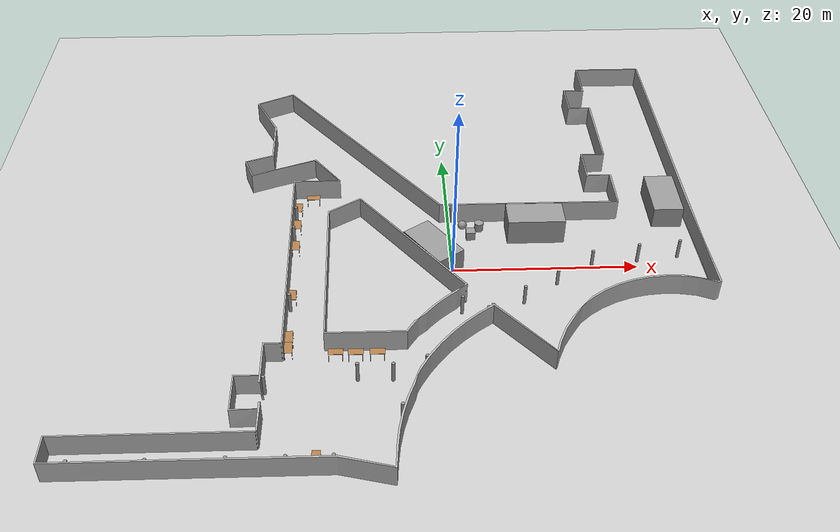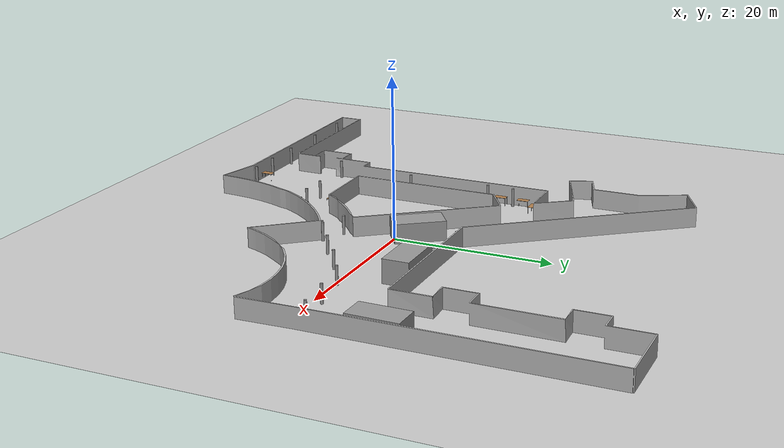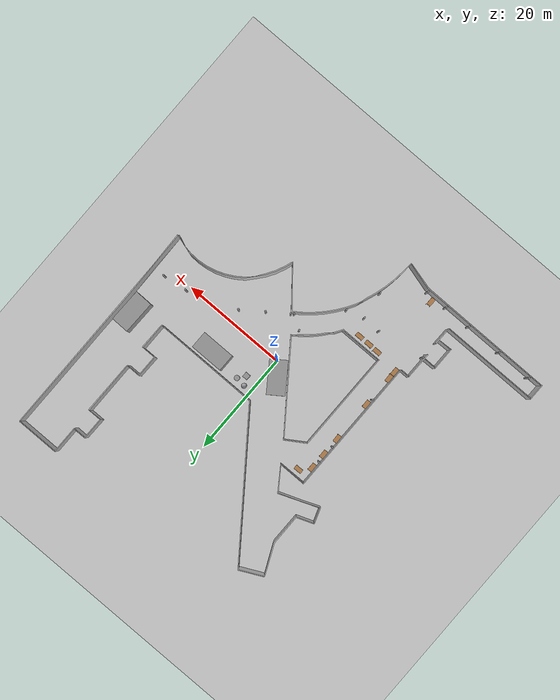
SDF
<sdf version="1.7">
 <world name="default">
  <light name="sun" type="directional">
   <pose>0 0 10 0 -0 0</pose>
   <diffuse>0.8 0.8 0.8 1</diffuse>
   <specular>0.2 0.2 0.2 1</specular>
   <attenuation>
    <range>1000</range>
    <constant>0.9</constant>
    <linear>0.01</linear>
    <quadratic>0.001</quadratic>
   </attenuation>
   <direction>-0.5 0.1 -0.9</direction>
   <spot><inner_angle>0</inner_angle><outer_angle>0</outer_angle><falloff>0</falloff></spot>
  </light>
  <model name="ground_plane">
   <static>1</static>
   <link name="link">
    <collision name="collision">
     <geometry><plane><normal>0 0 1</normal><size>100 100</size></plane></geometry>
     <surface>
      <contact><collide_bitmask>65535</collide_bitmask></contact>
      <friction><ode><mu>100</mu><mu2>50</mu2></ode></friction>
     </surface>
    </collision>
    <visual name="visual">
     <cast_shadows>0</cast_shadows>
     <geometry><plane><normal>0 0 1</normal><size>100 100</size></plane></geometry>
     <material>
      <script><uri>file://media/materials/scripts/gazebo.material</uri><name>Gazebo/Grey</name></script>
     </material>
    </visual>
   </link>
  </model>
  <gravity>0 0 -9.8</gravity>
  <magnetic_field>6e-06 2.3e-05 -4.2e-05</magnetic_field>
  <atmosphere type="adiabatic"/>
  <physics type="ode">
   <max_step_size>0.001</max_step_size>
   <real_time_factor>1</real_time_factor>
   <real_time_update_rate>1000</real_time_update_rate>
  </physics>
  <scene><ambient>0.4 0.4 0.4 1</ambient><background>0.7 0.7 0.7 1</background><shadows>1</shadows></scene>
  <audio><device>default</device></audio>
  <spherical_coordinates>
   <surface_model>EARTH_WGS84</surface_model>
   <latitude_deg>0</latitude_deg>
   <longitude_deg>0</longitude_deg>
   <elevation>0</elevation>
   <heading_deg>0</heading_deg>
  </spherical_coordinates>
  <model name="cw4">
   <static>1</static>
   <link name="link">
    <collision name="collision">
     <geometry><mesh><uri>model://dupa/meshes/mapa.stl</uri><scale>1 1 1</scale></mesh></geometry>
    </collision>
    <visual name="visual">
     <geometry><mesh><uri>model://dupa/meshes/mapa.stl</uri><scale>1 1 1</scale></mesh></geometry>
    </visual>
   </link>
   <pose>-2.21075 -1.90288 0 0 -0 0</pose>
  </model>
  <model name="Table">
   <static>1</static>
   <link name="link">
    <collision name="surface">
     <pose>0 0 1 0 -0 0</pose>
     <geometry><box><size>1.5 0.8 0.03</size></box></geometry>
     <surface><friction><ode><mu>0.6</mu><mu2>0.6</mu2></ode></friction></surface>
    </collision>
    <visual name="visual1">
     <pose>0 0 1 0 -0 0</pose>
     <geometry><box><size>1.5 0.8 0.03</size></box></geometry>
     <material>
      <diffuse>1 1 1 1</diffuse>
      <script><uri>file://media/materials/scripts/gazebo.material</uri><name>Gazebo/Wood</name></script>
      <pbr><metal><albedo_map>model://Table/Table_Diffuse.jpg</albedo_map></metal></pbr>
     </material>
    </visual>
    <collision name="front_left_leg">
     <pose>0.68 0.38 0.5 0 -0 0</pose>
     <geometry><cylinder><radius>0.02</radius><length>1</length></cylinder></geometry>
    </collision>
    <visual name="front_left_leg">
     <pose>0.68 0.38 0.5 0 -0 0</pose>
     <geometry><cylinder><radius>0.02</radius><length>1</length></cylinder></geometry>
     <material>
      <diffuse>0.5 0.5 0.5 1</diffuse>
      <script><uri>file://media/materials/scripts/gazebo.material</uri><name>Gazebo/Grey</name></script>
     </material>
    </visual>
    <collision name="front_right_leg">
     <pose>0.68 -0.38 0.5 0 -0 0</pose>
     <geometry><cylinder><radius>0.02</radius><length>1</length></cylinder></geometry>
    </collision>
    <visual name="front_right_leg">
     <pose>0.68 -0.38 0.5 0 -0 0</pose>
     <geometry><cylinder><radius>0.02</radius><length>1</length></cylinder></geometry>
     <material>
      <diffuse>0.5 0.5 0.5 1</diffuse>
      <script><uri>file://media/materials/scripts/gazebo.material</uri><name>Gazebo/Grey</name></script>
     </material>
    </visual>
    <collision name="back_right_leg">
     <pose>-0.68 -0.38 0.5 0 -0 0</pose>
     <geometry><cylinder><radius>0.02</radius><length>1</length></cylinder></geometry>
    </collision>
    <visual name="back_right_leg">
     <pose>-0.68 -0.38 0.5 0 -0 0</pose>
     <geometry><cylinder><radius>0.02</radius><length>1</length></cylinder></geometry>
     <material>
      <diffuse>0.5 0.5 0.5 1</diffuse>
      <script><uri>file://media/materials/scripts/gazebo.material</uri><name>Gazebo/Grey</name></script>
     </material>
    </visual>
    <collision name="back_left_leg">
     <pose>-0.68 0.38 0.5 0 -0 0</pose>
     <geometry><cylinder><radius>0.02</radius><length>1</length></cylinder></geometry>
    </collision>
    <visual name="back_left_leg">
     <pose>-0.68 0.38 0.5 0 -0 0</pose>
     <geometry><cylinder><radius>0.02</radius><length>1</length></cylinder></geometry>
     <material>
      <diffuse>0.5 0.5 0.5 1</diffuse>
      <script><uri>file://media/materials/scripts/gazebo.material</uri><name>Gazebo/Grey</name></script>
     </material>
    </visual>
   </link>
   <pose>-12.3632 -12.6824 0 0 -0 0</pose>
  </model>
  <model name="Table_0">
   <static>1</static>
   <link name="link">
    <collision name="surface">
     <pose>0 0 1 0 -0 0</pose>
     <geometry><box><size>1.5 0.8 0.03</size></box></geometry>
     <surface><friction><ode><mu>0.6</mu><mu2>0.6</mu2></ode></friction></surface>
    </collision>
    <visual name="visual1">
     <pose>0 0 1 0 -0 0</pose>
     <geometry><box><size>1.5 0.8 0.03</size></box></geometry>
     <material>
      <diffuse>1 1 1 1</diffuse>
      <script><uri>file://media/materials/scripts/gazebo.material</uri><name>Gazebo/Wood</name></script>
      <pbr><metal><albedo_map>model://Table/Table_Diffuse.jpg</albedo_map></metal></pbr>
     </material>
    </visual>
    <collision name="front_left_leg">
     <pose>0.68 0.38 0.5 0 -0 0</pose>
     <geometry><cylinder><radius>0.02</radius><length>1</length></cylinder></geometry>
    </collision>
    <visual name="front_left_leg">
     <pose>0.68 0.38 0.5 0 -0 0</pose>
     <geometry><cylinder><radius>0.02</radius><length>1</length></cylinder></geometry>
     <material>
      <diffuse>0.5 0.5 0.5 1</diffuse>
      <script><uri>file://media/materials/scripts/gazebo.material</uri><name>Gazebo/Grey</name></script>
     </material>
    </visual>
    <collision name="front_right_leg">
     <pose>0.68 -0.38 0.5 0 -0 0</pose>
     <geometry><cylinder><radius>0.02</radius><length>1</length></cylinder></geometry>
    </collision>
    <visual name="front_right_leg">
     <pose>0.68 -0.38 0.5 0 -0 0</pose>
     <geometry><cylinder><radius>0.02</radius><length>1</length></cylinder></geometry>
     <material>
      <diffuse>0.5 0.5 0.5 1</diffuse>
      <script><uri>file://media/materials/scripts/gazebo.material</uri><name>Gazebo/Grey</name></script>
     </material>
    </visual>
    <collision name="back_right_leg">
     <pose>-0.68 -0.38 0.5 0 -0 0</pose>
     <geometry><cylinder><radius>0.02</radius><length>1</length></cylinder></geometry>
    </collision>
    <visual name="back_right_leg">
     <pose>-0.68 -0.38 0.5 0 -0 0</pose>
     <geometry><cylinder><radius>0.02</radius><length>1</length></cylinder></geometry>
     <material>
      <diffuse>0.5 0.5 0.5 1</diffuse>
      <script><uri>file://media/materials/scripts/gazebo.material</uri><name>Gazebo/Grey</name></script>
     </material>
    </visual>
    <collision name="back_left_leg">
     <pose>-0.68 0.38 0.5 0 -0 0</pose>
     <geometry><cylinder><radius>0.02</radius><length>1</length></cylinder></geometry>
    </collision>
    <visual name="back_left_leg">
     <pose>-0.68 0.38 0.5 0 -0 0</pose>
     <geometry><cylinder><radius>0.02</radius><length>1</length></cylinder></geometry>
     <material>
      <diffuse>0.5 0.5 0.5 1</diffuse>
      <script><uri>file://media/materials/scripts/gazebo.material</uri><name>Gazebo/Grey</name></script>
     </material>
    </visual>
   </link>
   <pose>-10.4015 -12.7436 0 0 -0 0</pose>
  </model>
  <model name="Table_1">
   <static>1</static>
   <link name="link">
    <collision name="surface">
     <pose>0 0 1 0 -0 0</pose>
     <geometry><box><size>1.5 0.8 0.03</size></box></geometry>
     <surface><friction><ode><mu>0.6</mu><mu2>0.6</mu2></ode></friction></surface>
    </collision>
    <visual name="visual1">
     <pose>0 0 1 0 -0 0</pose>
     <geometry><box><size>1.5 0.8 0.03</size></box></geometry>
     <material>
      <diffuse>1 1 1 1</diffuse>
      <script><uri>file://media/materials/scripts/gazebo.material</uri><name>Gazebo/Wood</name></script>
      <pbr><metal><albedo_map>model://Table/Table_Diffuse.jpg</albedo_map></metal></pbr>
     </material>
    </visual>
    <collision name="front_left_leg">
     <pose>0.68 0.38 0.5 0 -0 0</pose>
     <geometry><cylinder><radius>0.02</radius><length>1</length></cylinder></geometry>
    </collision>
    <visual name="front_left_leg">
     <pose>0.68 0.38 0.5 0 -0 0</pose>
     <geometry><cylinder><radius>0.02</radius><length>1</length></cylinder></geometry>
     <material>
      <diffuse>0.5 0.5 0.5 1</diffuse>
      <script><uri>file://media/materials/scripts/gazebo.material</uri><name>Gazebo/Grey</name></script>
     </material>
    </visual>
    <collision name="front_right_leg">
     <pose>0.68 -0.38 0.5 0 -0 0</pose>
     <geometry><cylinder><radius>0.02</radius><length>1</length></cylinder></geometry>
    </collision>
    <visual name="front_right_leg">
     <pose>0.68 -0.38 0.5 0 -0 0</pose>
     <geometry><cylinder><radius>0.02</radius><length>1</length></cylinder></geometry>
     <material>
      <diffuse>0.5 0.5 0.5 1</diffuse>
      <script><uri>file://media/materials/scripts/gazebo.material</uri><name>Gazebo/Grey</name></script>
     </material>
    </visual>
    <collision name="back_right_leg">
     <pose>-0.68 -0.38 0.5 0 -0 0</pose>
     <geometry><cylinder><radius>0.02</radius><length>1</length></cylinder></geometry>
    </collision>
    <visual name="back_right_leg">
     <pose>-0.68 -0.38 0.5 0 -0 0</pose>
     <geometry><cylinder><radius>0.02</radius><length>1</length></cylinder></geometry>
     <material>
      <diffuse>0.5 0.5 0.5 1</diffuse>
      <script><uri>file://media/materials/scripts/gazebo.material</uri><name>Gazebo/Grey</name></script>
     </material>
    </visual>
    <collision name="back_left_leg">
     <pose>-0.68 0.38 0.5 0 -0 0</pose>
     <geometry><cylinder><radius>0.02</radius><length>1</length></cylinder></geometry>
    </collision>
    <visual name="back_left_leg">
     <pose>-0.68 0.38 0.5 0 -0 0</pose>
     <geometry><cylinder><radius>0.02</radius><length>1</length></cylinder></geometry>
     <material>
      <diffuse>0.5 0.5 0.5 1</diffuse>
      <script><uri>file://media/materials/scripts/gazebo.material</uri><name>Gazebo/Grey</name></script>
     </material>
    </visual>
   </link>
   <pose>-8.27464 -12.7467 0 0 -0 0</pose>
  </model>
  <model name="Table_2">
   <static>1</static>
   <link name="link">
    <collision name="surface">
     <pose>0 0 1 0 -0 0</pose>
     <geometry><box><size>1.5 0.8 0.03</size></box></geometry>
     <surface><friction><ode><mu>0.6</mu><mu2>0.6</mu2></ode></friction></surface>
    </collision>
    <visual name="visual1">
     <pose>0 0 1 0 -0 0</pose>
     <geometry><box><size>1.5 0.8 0.03</size></box></geometry>
     <material>
      <diffuse>1 1 1 1</diffuse>
      <script><uri>file://media/materials/scripts/gazebo.material</uri><name>Gazebo/Wood</name></script>
      <pbr><metal><albedo_map>model://Table/Table_Diffuse.jpg</albedo_map></metal></pbr>
     </material>
    </visual>
    <collision name="front_left_leg">
     <pose>0.68 0.38 0.5 0 -0 0</pose>
     <geometry><cylinder><radius>0.02</radius><length>1</length></cylinder></geometry>
    </collision>
    <visual name="front_left_leg">
     <pose>0.68 0.38 0.5 0 -0 0</pose>
     <geometry><cylinder><radius>0.02</radius><length>1</length></cylinder></geometry>
     <material>
      <diffuse>0.5 0.5 0.5 1</diffuse>
      <script><uri>file://media/materials/scripts/gazebo.material</uri><name>Gazebo/Grey</name></script>
     </material>
    </visual>
    <collision name="front_right_leg">
     <pose>0.68 -0.38 0.5 0 -0 0</pose>
     <geometry><cylinder><radius>0.02</radius><length>1</length></cylinder></geometry>
    </collision>
    <visual name="front_right_leg">
     <pose>0.68 -0.38 0.5 0 -0 0</pose>
     <geometry><cylinder><radius>0.02</radius><length>1</length></cylinder></geometry>
     <material>
      <diffuse>0.5 0.5 0.5 1</diffuse>
      <script><uri>file://media/materials/scripts/gazebo.material</uri><name>Gazebo/Grey</name></script>
     </material>
    </visual>
    <collision name="back_right_leg">
     <pose>-0.68 -0.38 0.5 0 -0 0</pose>
     <geometry><cylinder><radius>0.02</radius><length>1</length></cylinder></geometry>
    </collision>
    <visual name="back_right_leg">
     <pose>-0.68 -0.38 0.5 0 -0 0</pose>
     <geometry><cylinder><radius>0.02</radius><length>1</length></cylinder></geometry>
     <material>
      <diffuse>0.5 0.5 0.5 1</diffuse>
      <script><uri>file://media/materials/scripts/gazebo.material</uri><name>Gazebo/Grey</name></script>
     </material>
    </visual>
    <collision name="back_left_leg">
     <pose>-0.68 0.38 0.5 0 -0 0</pose>
     <geometry><cylinder><radius>0.02</radius><length>1</length></cylinder></geometry>
    </collision>
    <visual name="back_left_leg">
     <pose>-0.68 0.38 0.5 0 -0 0</pose>
     <geometry><cylinder><radius>0.02</radius><length>1</length></cylinder></geometry>
     <material>
      <diffuse>0.5 0.5 0.5 1</diffuse>
      <script><uri>file://media/materials/scripts/gazebo.material</uri><name>Gazebo/Grey</name></script>
     </material>
    </visual>
   </link>
   <pose>-13.8816 -25.5123 0 0 0 -1.58944</pose>
  </model>
  <model name="filar">
   <link name="link">
    <inertial>
     <mass>0.532177</mass>
     <inertia>
      <ixx>0.930096</ixx>
      <ixy>0</ixy>
      <ixz>0</ixz>
      <iyy>0.930096</iyy>
      <iyz>0</iyz>
      <izz>0.00774183</izz>
     </inertia>
    </inertial>
    <visual name="visual">
     <geometry><cylinder><radius>0.170572</radius><length>4.57005</length></cylinder></geometry>
     <material>
      <script><name>Gazebo/Grey</name><uri>file://media/materials/scripts/gazebo.material</uri></script>
      <shader type="pixel"/>
     </material>
    </visual>
    <collision name="collision">
     <geometry><cylinder><radius>0.170572</radius><length>4.57005</length></cylinder></geometry>
     <surface>
      <friction>
       <ode><mu>1</mu><mu2>1</mu2><fdir1>0 0 0</fdir1><slip1>0</slip1><slip2>0</slip2></ode>
       <torsional>
        <coefficient>1</coefficient>
        <patch_radius>0</patch_radius>
        <surface_radius>0</surface_radius>
        <use_patch_radius>1</use_patch_radius>
        <ode><slip>0</slip></ode>
       </torsional>
      </friction>
      <bounce><restitution_coefficient>0</restitution_coefficient><threshold>1e+06</threshold></bounce>
      <contact>
       <collide_without_contact>0</collide_without_contact>
       <collide_without_contact_bitmask>1</collide_without_contact_bitmask>
       <collide_bitmask>1</collide_bitmask>
       <ode>
        <soft_cfm>0</soft_cfm>
        <soft_erp>0.2</soft_erp>
        <kp>1e+13</kp>
        <kd>1</kd>
        <max_vel>0.01</max_vel>
        <min_depth>0</min_depth>
       </ode>
       <bullet>
        <split_impulse>1</split_impulse>
        <split_impulse_penetration_threshold>-0.01</split_impulse_penetration_threshold>
        <soft_cfm>0</soft_cfm>
        <soft_erp>0.2</soft_erp>
        <kp>1e+13</kp>
        <kd>1</kd>
       </bullet>
      </contact>
     </surface>
    </collision>
   </link>
   <static>0</static>
   <pose>-16.4504 -26.3002 0 0 -0 0</pose>
  </model>
  <model name="filar_0">
   <link name="link">
    <inertial>
     <mass>0.532177</mass>
     <inertia>
      <ixx>0.930096</ixx>
      <ixy>0</ixy>
      <ixz>0</ixz>
      <iyy>0.930096</iyy>
      <iyz>0</iyz>
      <izz>0.00774183</izz>
     </inertia>
    </inertial>
    <visual name="visual">
     <geometry><cylinder><radius>0.170572</radius><length>4.57005</length></cylinder></geometry>
     <material>
      <script><name>Gazebo/Grey</name><uri>file://media/materials/scripts/gazebo.material</uri></script>
      <shader type="pixel"/>
     </material>
    </visual>
    <collision name="collision">
     <geometry><cylinder><radius>0.170572</radius><length>4.57005</length></cylinder></geometry>
     <surface>
      <friction>
       <ode><mu>1</mu><mu2>1</mu2><fdir1>0 0 0</fdir1><slip1>0</slip1><slip2>0</slip2></ode>
       <torsional>
        <coefficient>1</coefficient>
        <patch_radius>0</patch_radius>
        <surface_radius>0</surface_radius>
        <use_patch_radius>1</use_patch_radius>
        <ode><slip>0</slip></ode>
       </torsional>
      </friction>
      <bounce><restitution_coefficient>0</restitution_coefficient><threshold>1e+06</threshold></bounce>
      <contact>
       <collide_without_contact>0</collide_without_contact>
       <collide_without_contact_bitmask>1</collide_without_contact_bitmask>
       <collide_bitmask>1</collide_bitmask>
       <ode>
        <soft_cfm>0</soft_cfm>
        <soft_erp>0.2</soft_erp>
        <kp>1e+13</kp>
        <kd>1</kd>
        <max_vel>0.01</max_vel>
        <min_depth>0</min_depth>
       </ode>
       <bullet>
        <split_impulse>1</split_impulse>
        <split_impulse_penetration_threshold>-0.01</split_impulse_penetration_threshold>
        <soft_cfm>0</soft_cfm>
        <soft_erp>0.2</soft_erp>
        <kp>1e+13</kp>
        <kd>1</kd>
       </bullet>
      </contact>
     </surface>
    </collision>
   </link>
   <static>0</static>
   <pose>-12.243 -26.276 0 0 -0 0</pose>
  </model>
  <model name="filar_1">
   <link name="link">
    <inertial>
     <mass>0.532177</mass>
     <inertia>
      <ixx>0.930096</ixx>
      <ixy>0</ixy>
      <ixz>0</ixz>
      <iyy>0.930096</iyy>
      <iyz>0</iyz>
      <izz>0.00774183</izz>
     </inertia>
    </inertial>
    <visual name="visual">
     <geometry><cylinder><radius>0.170572</radius><length>4.57005</length></cylinder></geometry>
     <material>
      <script><name>Gazebo/Grey</name><uri>file://media/materials/scripts/gazebo.material</uri></script>
      <shader type="pixel"/>
     </material>
    </visual>
    <collision name="collision">
     <geometry><cylinder><radius>0.170572</radius><length>4.57005</length></cylinder></geometry>
     <surface>
      <friction>
       <ode><mu>1</mu><mu2>1</mu2><fdir1>0 0 0</fdir1><slip1>0</slip1><slip2>0</slip2></ode>
       <torsional>
        <coefficient>1</coefficient>
        <patch_radius>0</patch_radius>
        <surface_radius>0</surface_radius>
        <use_patch_radius>1</use_patch_radius>
        <ode><slip>0</slip></ode>
       </torsional>
      </friction>
      <bounce><restitution_coefficient>0</restitution_coefficient><threshold>1e+06</threshold></bounce>
      <contact>
       <collide_without_contact>0</collide_without_contact>
       <collide_without_contact_bitmask>1</collide_without_contact_bitmask>
       <collide_bitmask>1</collide_bitmask>
       <ode>
        <soft_cfm>0</soft_cfm>
        <soft_erp>0.2</soft_erp>
        <kp>1e+13</kp>
        <kd>1</kd>
        <max_vel>0.01</max_vel>
        <min_depth>0</min_depth>
       </ode>
       <bullet>
        <split_impulse>1</split_impulse>
        <split_impulse_penetration_threshold>-0.01</split_impulse_penetration_threshold>
        <soft_cfm>0</soft_cfm>
        <soft_erp>0.2</soft_erp>
        <kp>1e+13</kp>
        <kd>1</kd>
       </bullet>
      </contact>
     </surface>
    </collision>
   </link>
   <static>0</static>
   <pose>-19.0227 -16.9486 0 0 -0 0</pose>
  </model>
  <model name="filar_2">
   <link name="link">
    <inertial>
     <mass>0.532177</mass>
     <inertia>
      <ixx>0.930096</ixx>
      <ixy>0</ixy>
      <ixz>0</ixz>
      <iyy>0.930096</iyy>
      <iyz>0</iyz>
      <izz>0.00774183</izz>
     </inertia>
    </inertial>
    <visual name="visual">
     <geometry><cylinder><radius>0.170572</radius><length>4.57005</length></cylinder></geometry>
     <material>
      <script><name>Gazebo/Grey</name><uri>file://media/materials/scripts/gazebo.material</uri></script>
      <shader type="pixel"/>
     </material>
    </visual>
    <collision name="collision">
     <geometry><cylinder><radius>0.170572</radius><length>4.57005</length></cylinder></geometry>
     <surface>
      <friction>
       <ode><mu>1</mu><mu2>1</mu2><fdir1>0 0 0</fdir1><slip1>0</slip1><slip2>0</slip2></ode>
       <torsional>
        <coefficient>1</coefficient>
        <patch_radius>0</patch_radius>
        <surface_radius>0</surface_radius>
        <use_patch_radius>1</use_patch_radius>
        <ode><slip>0</slip></ode>
       </torsional>
      </friction>
      <bounce><restitution_coefficient>0</restitution_coefficient><threshold>1e+06</threshold></bounce>
      <contact>
       <collide_without_contact>0</collide_without_contact>
       <collide_without_contact_bitmask>1</collide_without_contact_bitmask>
       <collide_bitmask>1</collide_bitmask>
       <ode>
        <soft_cfm>0</soft_cfm>
        <soft_erp>0.2</soft_erp>
        <kp>1e+13</kp>
        <kd>1</kd>
        <max_vel>0.01</max_vel>
        <min_depth>0</min_depth>
       </ode>
       <bullet>
        <split_impulse>1</split_impulse>
        <split_impulse_penetration_threshold>-0.01</split_impulse_penetration_threshold>
        <soft_cfm>0</soft_cfm>
        <soft_erp>0.2</soft_erp>
        <kp>1e+13</kp>
        <kd>1</kd>
       </bullet>
      </contact>
     </surface>
    </collision>
   </link>
   <static>0</static>
   <pose>-10.2111 -15.5124 0 0 -0 0</pose>
  </model>
  <model name="filar_3">
   <link name="link">
    <inertial>
     <mass>0.532177</mass>
     <inertia>
      <ixx>0.930096</ixx>
      <ixy>0</ixy>
      <ixz>0</ixz>
      <iyy>0.930096</iyy>
      <iyz>0</iyz>
      <izz>0.00774183</izz>
     </inertia>
    </inertial>
    <visual name="visual">
     <geometry><cylinder><radius>0.170572</radius><length>4.57005</length></cylinder></geometry>
     <material>
      <script><name>Gazebo/Grey</name><uri>file://media/materials/scripts/gazebo.material</uri></script>
      <shader type="pixel"/>
     </material>
    </visual>
    <collision name="collision">
     <geometry><cylinder><radius>0.170572</radius><length>4.57005</length></cylinder></geometry>
     <surface>
      <friction>
       <ode><mu>1</mu><mu2>1</mu2><fdir1>0 0 0</fdir1><slip1>0</slip1><slip2>0</slip2></ode>
       <torsional>
        <coefficient>1</coefficient>
        <patch_radius>0</patch_radius>
        <surface_radius>0</surface_radius>
        <use_patch_radius>1</use_patch_radius>
        <ode><slip>0</slip></ode>
       </torsional>
      </friction>
      <bounce><restitution_coefficient>0</restitution_coefficient><threshold>1e+06</threshold></bounce>
      <contact>
       <collide_without_contact>0</collide_without_contact>
       <collide_without_contact_bitmask>1</collide_without_contact_bitmask>
       <collide_bitmask>1</collide_bitmask>
       <ode>
        <soft_cfm>0</soft_cfm>
        <soft_erp>0.2</soft_erp>
        <kp>1e+13</kp>
        <kd>1</kd>
        <max_vel>0.01</max_vel>
        <min_depth>0</min_depth>
       </ode>
       <bullet>
        <split_impulse>1</split_impulse>
        <split_impulse_penetration_threshold>-0.01</split_impulse_penetration_threshold>
        <soft_cfm>0</soft_cfm>
        <soft_erp>0.2</soft_erp>
        <kp>1e+13</kp>
        <kd>1</kd>
       </bullet>
      </contact>
     </surface>
    </collision>
   </link>
   <static>0</static>
   <pose>-6.7867 -15.6078 0 0 -0 0</pose>
  </model>
  <model name="filar_4">
   <link name="link">
    <inertial>
     <mass>0.532177</mass>
     <inertia>
      <ixx>0.930096</ixx>
      <ixy>0</ixy>
      <ixz>0</ixz>
      <iyy>0.930096</iyy>
      <iyz>0</iyz>
      <izz>0.00774183</izz>
     </inertia>
    </inertial>
    <visual name="visual">
     <geometry><cylinder><radius>0.170572</radius><length>4.57005</length></cylinder></geometry>
     <material>
      <script><name>Gazebo/Grey</name><uri>file://media/materials/scripts/gazebo.material</uri></script>
      <shader type="pixel"/>
     </material>
    </visual>
    <collision name="collision">
     <geometry><cylinder><radius>0.170572</radius><length>4.57005</length></cylinder></geometry>
     <surface>
      <friction>
       <ode><mu>1</mu><mu2>1</mu2><fdir1>0 0 0</fdir1><slip1>0</slip1><slip2>0</slip2></ode>
       <torsional>
        <coefficient>1</coefficient>
        <patch_radius>0</patch_radius>
        <surface_radius>0</surface_radius>
        <use_patch_radius>1</use_patch_radius>
        <ode><slip>0</slip></ode>
       </torsional>
      </friction>
      <bounce><restitution_coefficient>0</restitution_coefficient><threshold>1e+06</threshold></bounce>
      <contact>
       <collide_without_contact>0</collide_without_contact>
       <collide_without_contact_bitmask>1</collide_without_contact_bitmask>
       <collide_bitmask>1</collide_bitmask>
       <ode>
        <soft_cfm>0</soft_cfm>
        <soft_erp>0.2</soft_erp>
        <kp>1e+13</kp>
        <kd>1</kd>
        <max_vel>0.01</max_vel>
        <min_depth>0</min_depth>
       </ode>
       <bullet>
        <split_impulse>1</split_impulse>
        <split_impulse_penetration_threshold>-0.01</split_impulse_penetration_threshold>
        <soft_cfm>0</soft_cfm>
        <soft_erp>0.2</soft_erp>
        <kp>1e+13</kp>
        <kd>1</kd>
       </bullet>
      </contact>
     </surface>
    </collision>
   </link>
   <static>0</static>
   <pose>-3.49321 -14.6513 0 0 -0 0</pose>
  </model>
  <model name="filar_5">
   <link name="link">
    <inertial>
     <mass>0.532177</mass>
     <inertia>
      <ixx>0.930096</ixx>
      <ixy>0</ixy>
      <ixz>0</ixz>
      <iyy>0.930096</iyy>
      <iyz>0</iyz>
      <izz>0.00774183</izz>
     </inertia>
    </inertial>
    <visual name="visual">
     <geometry><cylinder><radius>0.170572</radius><length>4.57005</length></cylinder></geometry>
     <material>
      <script><name>Gazebo/Grey</name><uri>file://media/materials/scripts/gazebo.material</uri></script>
      <shader type="pixel"/>
     </material>
    </visual>
    <collision name="collision">
     <geometry><cylinder><radius>0.170572</radius><length>4.57005</length></cylinder></geometry>
     <surface>
      <friction>
       <ode><mu>1</mu><mu2>1</mu2><fdir1>0 0 0</fdir1><slip1>0</slip1><slip2>0</slip2></ode>
       <torsional>
        <coefficient>1</coefficient>
        <patch_radius>0</patch_radius>
        <surface_radius>0</surface_radius>
        <use_patch_radius>1</use_patch_radius>
        <ode><slip>0</slip></ode>
       </torsional>
      </friction>
      <bounce><restitution_coefficient>0</restitution_coefficient><threshold>1e+06</threshold></bounce>
      <contact>
       <collide_without_contact>0</collide_without_contact>
       <collide_without_contact_bitmask>1</collide_without_contact_bitmask>
       <collide_bitmask>1</collide_bitmask>
       <ode>
        <soft_cfm>0</soft_cfm>
        <soft_erp>0.2</soft_erp>
        <kp>1e+13</kp>
        <kd>1</kd>
        <max_vel>0.01</max_vel>
        <min_depth>0</min_depth>
       </ode>
       <bullet>
        <split_impulse>1</split_impulse>
        <split_impulse_penetration_threshold>-0.01</split_impulse_penetration_threshold>
        <soft_cfm>0</soft_cfm>
        <soft_erp>0.2</soft_erp>
        <kp>1e+13</kp>
        <kd>1</kd>
       </bullet>
      </contact>
     </surface>
    </collision>
   </link>
   <static>0</static>
   <pose>-6.04874 -20.6463 0 0 -0 0</pose>
  </model>
  <model name="filar_6">
   <link name="link">
    <inertial>
     <mass>0.532177</mass>
     <inertia>
      <ixx>0.930096</ixx>
      <ixy>0</ixy>
      <ixz>0</ixz>
      <iyy>0.930096</iyy>
      <iyz>0</iyz>
      <izz>0.00774183</izz>
     </inertia>
    </inertial>
    <visual name="visual">
     <geometry><cylinder><radius>0.170572</radius><length>4.57005</length></cylinder></geometry>
     <material>
      <script><name>Gazebo/Grey</name><uri>file://media/materials/scripts/gazebo.material</uri></script>
      <shader type="pixel"/>
     </material>
    </visual>
    <collision name="collision">
     <geometry><cylinder><radius>0.170572</radius><length>4.57005</length></cylinder></geometry>
     <surface>
      <friction>
       <ode><mu>1</mu><mu2>1</mu2><fdir1>0 0 0</fdir1><slip1>0</slip1><slip2>0</slip2></ode>
       <torsional>
        <coefficient>1</coefficient>
        <patch_radius>0</patch_radius>
        <surface_radius>0</surface_radius>
        <use_patch_radius>1</use_patch_radius>
        <ode><slip>0</slip></ode>
       </torsional>
      </friction>
      <bounce><restitution_coefficient>0</restitution_coefficient><threshold>1e+06</threshold></bounce>
      <contact>
       <collide_without_contact>0</collide_without_contact>
       <collide_without_contact_bitmask>1</collide_without_contact_bitmask>
       <collide_bitmask>1</collide_bitmask>
       <ode>
        <soft_cfm>0</soft_cfm>
        <soft_erp>0.2</soft_erp>
        <kp>1e+13</kp>
        <kd>1</kd>
        <max_vel>0.01</max_vel>
        <min_depth>0</min_depth>
       </ode>
       <bullet>
        <split_impulse>1</split_impulse>
        <split_impulse_penetration_threshold>-0.01</split_impulse_penetration_threshold>
        <soft_cfm>0</soft_cfm>
        <soft_erp>0.2</soft_erp>
        <kp>1e+13</kp>
        <kd>1</kd>
       </bullet>
      </contact>
     </surface>
    </collision>
   </link>
   <static>0</static>
   <pose>-21.6453 -26.3087 0 0 -0 0</pose>
  </model>
  <model name="filar_7">
   <link name="link">
    <inertial>
     <mass>0.532177</mass>
     <inertia>
      <ixx>0.930096</ixx>
      <ixy>0</ixy>
      <ixz>0</ixz>
      <iyy>0.930096</iyy>
      <iyz>0</iyz>
      <izz>0.00774183</izz>
     </inertia>
    </inertial>
    <visual name="visual">
     <geometry><cylinder><radius>0.170572</radius><length>4.57005</length></cylinder></geometry>
     <material>
      <script><name>Gazebo/Grey</name><uri>file://media/materials/scripts/gazebo.material</uri></script>
      <shader type="pixel"/>
     </material>
    </visual>
    <collision name="collision">
     <geometry><cylinder><radius>0.170572</radius><length>4.57005</length></cylinder></geometry>
     <surface>
      <friction>
       <ode><mu>1</mu><mu2>1</mu2><fdir1>0 0 0</fdir1><slip1>0</slip1><slip2>0</slip2></ode>
       <torsional>
        <coefficient>1</coefficient>
        <patch_radius>0</patch_radius>
        <surface_radius>0</surface_radius>
        <use_patch_radius>1</use_patch_radius>
        <ode><slip>0</slip></ode>
       </torsional>
      </friction>
      <bounce><restitution_coefficient>0</restitution_coefficient><threshold>1e+06</threshold></bounce>
      <contact>
       <collide_without_contact>0</collide_without_contact>
       <collide_without_contact_bitmask>1</collide_without_contact_bitmask>
       <collide_bitmask>1</collide_bitmask>
       <ode>
        <soft_cfm>0</soft_cfm>
        <soft_erp>0.2</soft_erp>
        <kp>1e+13</kp>
        <kd>1</kd>
        <max_vel>0.01</max_vel>
        <min_depth>0</min_depth>
       </ode>
       <bullet>
        <split_impulse>1</split_impulse>
        <split_impulse_penetration_threshold>-0.01</split_impulse_penetration_threshold>
        <soft_cfm>0</soft_cfm>
        <soft_erp>0.2</soft_erp>
        <kp>1e+13</kp>
        <kd>1</kd>
       </bullet>
      </contact>
     </surface>
    </collision>
   </link>
   <static>0</static>
   <pose>-28.6172 -26.3131 0 0 -0 0</pose>
  </model>
  <model name="filar_8">
   <link name="link">
    <inertial>
     <mass>0.532177</mass>
     <inertia>
      <ixx>0.930096</ixx>
      <ixy>0</ixy>
      <ixz>0</ixz>
      <iyy>0.930096</iyy>
      <iyz>0</iyz>
      <izz>0.00774183</izz>
     </inertia>
    </inertial>
    <visual name="visual">
     <geometry><cylinder><radius>0.170572</radius><length>4.57005</length></cylinder></geometry>
     <material>
      <script><name>Gazebo/Grey</name><uri>file://media/materials/scripts/gazebo.material</uri></script>
      <shader type="pixel"/>
     </material>
    </visual>
    <collision name="collision">
     <geometry><cylinder><radius>0.170572</radius><length>4.57005</length></cylinder></geometry>
     <surface>
      <friction>
       <ode><mu>1</mu><mu2>1</mu2><fdir1>0 0 0</fdir1><slip1>0</slip1><slip2>0</slip2></ode>
       <torsional>
        <coefficient>1</coefficient>
        <patch_radius>0</patch_radius>
        <surface_radius>0</surface_radius>
        <use_patch_radius>1</use_patch_radius>
        <ode><slip>0</slip></ode>
       </torsional>
      </friction>
      <bounce><restitution_coefficient>0</restitution_coefficient><threshold>1e+06</threshold></bounce>
      <contact>
       <collide_without_contact>0</collide_without_contact>
       <collide_without_contact_bitmask>1</collide_without_contact_bitmask>
       <collide_bitmask>1</collide_bitmask>
       <ode>
        <soft_cfm>0</soft_cfm>
        <soft_erp>0.2</soft_erp>
        <kp>1e+13</kp>
        <kd>1</kd>
        <max_vel>0.01</max_vel>
        <min_depth>0</min_depth>
       </ode>
       <bullet>
        <split_impulse>1</split_impulse>
        <split_impulse_penetration_threshold>-0.01</split_impulse_penetration_threshold>
        <soft_cfm>0</soft_cfm>
        <soft_erp>0.2</soft_erp>
        <kp>1e+13</kp>
        <kd>1</kd>
       </bullet>
      </contact>
     </surface>
    </collision>
   </link>
   <static>0</static>
   <pose>-35.4082 -26.2886 0 0 -0 0</pose>
  </model>
  <model name="Table_3">
   <static>1</static>
   <link name="link">
    <collision name="surface">
     <pose>0 0 1 0 -0 0</pose>
     <geometry><box><size>1.5 0.8 0.03</size></box></geometry>
     <surface><friction><ode><mu>0.6</mu><mu2>0.6</mu2></ode></friction></surface>
    </collision>
    <visual name="visual1">
     <pose>0 0 1 0 -0 0</pose>
     <geometry><box><size>1.5 0.8 0.03</size></box></geometry>
     <material>
      <diffuse>1 1 1 1</diffuse>
      <script><uri>file://media/materials/scripts/gazebo.material</uri><name>Gazebo/Wood</name></script>
      <pbr><metal><albedo_map>model://Table/Table_Diffuse.jpg</albedo_map></metal></pbr>
     </material>
    </visual>
    <collision name="front_left_leg">
     <pose>0.68 0.38 0.5 0 -0 0</pose>
     <geometry><cylinder><radius>0.02</radius><length>1</length></cylinder></geometry>
    </collision>
    <visual name="front_left_leg">
     <pose>0.68 0.38 0.5 0 -0 0</pose>
     <geometry><cylinder><radius>0.02</radius><length>1</length></cylinder></geometry>
     <material>
      <diffuse>0.5 0.5 0.5 1</diffuse>
      <script><uri>file://media/materials/scripts/gazebo.material</uri><name>Gazebo/Grey</name></script>
     </material>
    </visual>
    <collision name="front_right_leg">
     <pose>0.68 -0.38 0.5 0 -0 0</pose>
     <geometry><cylinder><radius>0.02</radius><length>1</length></cylinder></geometry>
    </collision>
    <visual name="front_right_leg">
     <pose>0.68 -0.38 0.5 0 -0 0</pose>
     <geometry><cylinder><radius>0.02</radius><length>1</length></cylinder></geometry>
     <material>
      <diffuse>0.5 0.5 0.5 1</diffuse>
      <script><uri>file://media/materials/scripts/gazebo.material</uri><name>Gazebo/Grey</name></script>
     </material>
    </visual>
    <collision name="back_right_leg">
     <pose>-0.68 -0.38 0.5 0 -0 0</pose>
     <geometry><cylinder><radius>0.02</radius><length>1</length></cylinder></geometry>
    </collision>
    <visual name="back_right_leg">
     <pose>-0.68 -0.38 0.5 0 -0 0</pose>
     <geometry><cylinder><radius>0.02</radius><length>1</length></cylinder></geometry>
     <material>
      <diffuse>0.5 0.5 0.5 1</diffuse>
      <script><uri>file://media/materials/scripts/gazebo.material</uri><name>Gazebo/Grey</name></script>
     </material>
    </visual>
    <collision name="back_left_leg">
     <pose>-0.68 0.38 0.5 0 -0 0</pose>
     <geometry><cylinder><radius>0.02</radius><length>1</length></cylinder></geometry>
    </collision>
    <visual name="back_left_leg">
     <pose>-0.68 0.38 0.5 0 -0 0</pose>
     <geometry><cylinder><radius>0.02</radius><length>1</length></cylinder></geometry>
     <material>
      <diffuse>0.5 0.5 0.5 1</diffuse>
      <script><uri>file://media/materials/scripts/gazebo.material</uri><name>Gazebo/Grey</name></script>
     </material>
    </visual>
   </link>
   <pose>-17.0236 -11.9977 0 0 0 -1.54257</pose>
  </model>
  <model name="Table_3_clone">
   <static>1</static>
   <link name="link">
    <collision name="surface">
     <pose>0 0 1 0 -0 0</pose>
     <geometry><box><size>1.5 0.8 0.03</size></box></geometry>
     <surface><friction><ode><mu>0.6</mu><mu2>0.6</mu2></ode></friction></surface>
    </collision>
    <visual name="visual1">
     <pose>0 0 1 0 -0 0</pose>
     <geometry><box><size>1.5 0.8 0.03</size></box></geometry>
     <material>
      <diffuse>1 1 1 1</diffuse>
      <script><uri>file://media/materials/scripts/gazebo.material</uri><name>Gazebo/Wood</name></script>
      <pbr><metal><albedo_map>model://Table/Table_Diffuse.jpg</albedo_map></metal></pbr>
     </material>
    </visual>
    <collision name="front_left_leg">
     <pose>0.68 0.38 0.5 0 -0 0</pose>
     <geometry><cylinder><radius>0.02</radius><length>1</length></cylinder></geometry>
    </collision>
    <visual name="front_left_leg">
     <pose>0.68 0.38 0.5 0 -0 0</pose>
     <geometry><cylinder><radius>0.02</radius><length>1</length></cylinder></geometry>
     <material>
      <diffuse>0.5 0.5 0.5 1</diffuse>
      <script><uri>file://media/materials/scripts/gazebo.material</uri><name>Gazebo/Grey</name></script>
     </material>
    </visual>
    <collision name="front_right_leg">
     <pose>0.68 -0.38 0.5 0 -0 0</pose>
     <geometry><cylinder><radius>0.02</radius><length>1</length></cylinder></geometry>
    </collision>
    <visual name="front_right_leg">
     <pose>0.68 -0.38 0.5 0 -0 0</pose>
     <geometry><cylinder><radius>0.02</radius><length>1</length></cylinder></geometry>
     <material>
      <diffuse>0.5 0.5 0.5 1</diffuse>
      <script><uri>file://media/materials/scripts/gazebo.material</uri><name>Gazebo/Grey</name></script>
     </material>
    </visual>
    <collision name="back_right_leg">
     <pose>-0.68 -0.38 0.5 0 -0 0</pose>
     <geometry><cylinder><radius>0.02</radius><length>1</length></cylinder></geometry>
    </collision>
    <visual name="back_right_leg">
     <pose>-0.68 -0.38 0.5 0 -0 0</pose>
     <geometry><cylinder><radius>0.02</radius><length>1</length></cylinder></geometry>
     <material>
      <diffuse>0.5 0.5 0.5 1</diffuse>
      <script><uri>file://media/materials/scripts/gazebo.material</uri><name>Gazebo/Grey</name></script>
     </material>
    </visual>
    <collision name="back_left_leg">
     <pose>-0.68 0.38 0.5 0 -0 0</pose>
     <geometry><cylinder><radius>0.02</radius><length>1</length></cylinder></geometry>
    </collision>
    <visual name="back_left_leg">
     <pose>-0.68 0.38 0.5 0 -0 0</pose>
     <geometry><cylinder><radius>0.02</radius><length>1</length></cylinder></geometry>
     <material>
      <diffuse>0.5 0.5 0.5 1</diffuse>
      <script><uri>file://media/materials/scripts/gazebo.material</uri><name>Gazebo/Grey</name></script>
     </material>
    </visual>
   </link>
   <pose>-17.0259 -10.4756 0 0 0 -1.54257</pose>
  </model>
  <model name="filar_9">
   <link name="link">
    <inertial>
     <mass>0.532177</mass>
     <inertia>
      <ixx>0.930096</ixx>
      <ixy>0</ixy>
      <ixz>0</ixz>
      <iyy>0.930096</iyy>
      <iyz>0</iyz>
      <izz>0.00774183</izz>
     </inertia>
    </inertial>
    <visual name="visual">
     <geometry><cylinder><radius>0.170572</radius><length>4.57005</length></cylinder></geometry>
     <material>
      <script><name>Gazebo/Grey</name><uri>file://media/materials/scripts/gazebo.material</uri></script>
      <shader type="pixel"/>
     </material>
    </visual>
    <collision name="collision">
     <geometry><cylinder><radius>0.170572</radius><length>4.57005</length></cylinder></geometry>
     <surface>
      <friction>
       <ode><mu>1</mu><mu2>1</mu2><fdir1>0 0 0</fdir1><slip1>0</slip1><slip2>0</slip2></ode>
       <torsional>
        <coefficient>1</coefficient>
        <patch_radius>0</patch_radius>
        <surface_radius>0</surface_radius>
        <use_patch_radius>1</use_patch_radius>
        <ode><slip>0</slip></ode>
       </torsional>
      </friction>
      <bounce><restitution_coefficient>0</restitution_coefficient><threshold>1e+06</threshold></bounce>
      <contact>
       <collide_without_contact>0</collide_without_contact>
       <collide_without_contact_bitmask>1</collide_without_contact_bitmask>
       <collide_bitmask>1</collide_bitmask>
       <ode>
        <soft_cfm>0</soft_cfm>
        <soft_erp>0.2</soft_erp>
        <kp>1e+13</kp>
        <kd>1</kd>
        <max_vel>0.01</max_vel>
        <min_depth>0</min_depth>
       </ode>
       <bullet>
        <split_impulse>1</split_impulse>
        <split_impulse_penetration_threshold>-0.01</split_impulse_penetration_threshold>
        <soft_cfm>0</soft_cfm>
        <soft_erp>0.2</soft_erp>
        <kp>1e+13</kp>
        <kd>1</kd>
       </bullet>
      </contact>
     </surface>
    </collision>
   </link>
   <static>0</static>
   <pose>-17.1599 -5.65048 0 0 -0 0</pose>
  </model>
  <model name="Table_3_clone_0">
   <static>1</static>
   <link name="link">
    <collision name="surface">
     <pose>0 0 1 0 -0 0</pose>
     <geometry><box><size>1.5 0.8 0.03</size></box></geometry>
     <surface><friction><ode><mu>0.6</mu><mu2>0.6</mu2></ode></friction></surface>
    </collision>
    <visual name="visual1">
     <pose>0 0 1 0 -0 0</pose>
     <geometry><box><size>1.5 0.8 0.03</size></box></geometry>
     <material>
      <diffuse>1 1 1 1</diffuse>
      <script><uri>file://media/materials/scripts/gazebo.material</uri><name>Gazebo/Wood</name></script>
      <pbr><metal><albedo_map>model://Table/Table_Diffuse.jpg</albedo_map></metal></pbr>
     </material>
    </visual>
    <collision name="front_left_leg">
     <pose>0.68 0.38 0.5 0 -0 0</pose>
     <geometry><cylinder><radius>0.02</radius><length>1</length></cylinder></geometry>
    </collision>
    <visual name="front_left_leg">
     <pose>0.68 0.38 0.5 0 -0 0</pose>
     <geometry><cylinder><radius>0.02</radius><length>1</length></cylinder></geometry>
     <material>
      <diffuse>0.5 0.5 0.5 1</diffuse>
      <script><uri>file://media/materials/scripts/gazebo.material</uri><name>Gazebo/Grey</name></script>
     </material>
    </visual>
    <collision name="front_right_leg">
     <pose>0.68 -0.38 0.5 0 -0 0</pose>
     <geometry><cylinder><radius>0.02</radius><length>1</length></cylinder></geometry>
    </collision>
    <visual name="front_right_leg">
     <pose>0.68 -0.38 0.5 0 -0 0</pose>
     <geometry><cylinder><radius>0.02</radius><length>1</length></cylinder></geometry>
     <material>
      <diffuse>0.5 0.5 0.5 1</diffuse>
      <script><uri>file://media/materials/scripts/gazebo.material</uri><name>Gazebo/Grey</name></script>
     </material>
    </visual>
    <collision name="back_right_leg">
     <pose>-0.68 -0.38 0.5 0 -0 0</pose>
     <geometry><cylinder><radius>0.02</radius><length>1</length></cylinder></geometry>
    </collision>
    <visual name="back_right_leg">
     <pose>-0.68 -0.38 0.5 0 -0 0</pose>
     <geometry><cylinder><radius>0.02</radius><length>1</length></cylinder></geometry>
     <material>
      <diffuse>0.5 0.5 0.5 1</diffuse>
      <script><uri>file://media/materials/scripts/gazebo.material</uri><name>Gazebo/Grey</name></script>
     </material>
    </visual>
    <collision name="back_left_leg">
     <pose>-0.68 0.38 0.5 0 -0 0</pose>
     <geometry><cylinder><radius>0.02</radius><length>1</length></cylinder></geometry>
    </collision>
    <visual name="back_left_leg">
     <pose>-0.68 0.38 0.5 0 -0 0</pose>
     <geometry><cylinder><radius>0.02</radius><length>1</length></cylinder></geometry>
     <material>
      <diffuse>0.5 0.5 0.5 1</diffuse>
      <script><uri>file://media/materials/scripts/gazebo.material</uri><name>Gazebo/Grey</name></script>
     </material>
    </visual>
   </link>
   <pose>-16.9686 -4.41044 0 0 0 -1.54257</pose>
  </model>
  <model name="Table_3_clone_1">
   <static>1</static>
   <link name="link">
    <collision name="surface">
     <pose>0 0 1 0 -0 0</pose>
     <geometry><box><size>1.5 0.8 0.03</size></box></geometry>
     <surface><friction><ode><mu>0.6</mu><mu2>0.6</mu2></ode></friction></surface>
    </collision>
    <visual name="visual1">
     <pose>0 0 1 0 -0 0</pose>
     <geometry><box><size>1.5 0.8 0.03</size></box></geometry>
     <material>
      <diffuse>1 1 1 1</diffuse>
      <script><uri>file://media/materials/scripts/gazebo.material</uri><name>Gazebo/Wood</name></script>
      <pbr><metal><albedo_map>model://Table/Table_Diffuse.jpg</albedo_map></metal></pbr>
     </material>
    </visual>
    <collision name="front_left_leg">
     <pose>0.68 0.38 0.5 0 -0 0</pose>
     <geometry><cylinder><radius>0.02</radius><length>1</length></cylinder></geometry>
    </collision>
    <visual name="front_left_leg">
     <pose>0.68 0.38 0.5 0 -0 0</pose>
     <geometry><cylinder><radius>0.02</radius><length>1</length></cylinder></geometry>
     <material>
      <diffuse>0.5 0.5 0.5 1</diffuse>
      <script><uri>file://media/materials/scripts/gazebo.material</uri><name>Gazebo/Grey</name></script>
     </material>
    </visual>
    <collision name="front_right_leg">
     <pose>0.68 -0.38 0.5 0 -0 0</pose>
     <geometry><cylinder><radius>0.02</radius><length>1</length></cylinder></geometry>
    </collision>
    <visual name="front_right_leg">
     <pose>0.68 -0.38 0.5 0 -0 0</pose>
     <geometry><cylinder><radius>0.02</radius><length>1</length></cylinder></geometry>
     <material>
      <diffuse>0.5 0.5 0.5 1</diffuse>
      <script><uri>file://media/materials/scripts/gazebo.material</uri><name>Gazebo/Grey</name></script>
     </material>
    </visual>
    <collision name="back_right_leg">
     <pose>-0.68 -0.38 0.5 0 -0 0</pose>
     <geometry><cylinder><radius>0.02</radius><length>1</length></cylinder></geometry>
    </collision>
    <visual name="back_right_leg">
     <pose>-0.68 -0.38 0.5 0 -0 0</pose>
     <geometry><cylinder><radius>0.02</radius><length>1</length></cylinder></geometry>
     <material>
      <diffuse>0.5 0.5 0.5 1</diffuse>
      <script><uri>file://media/materials/scripts/gazebo.material</uri><name>Gazebo/Grey</name></script>
     </material>
    </visual>
    <collision name="back_left_leg">
     <pose>-0.68 0.38 0.5 0 -0 0</pose>
     <geometry><cylinder><radius>0.02</radius><length>1</length></cylinder></geometry>
    </collision>
    <visual name="back_left_leg">
     <pose>-0.68 0.38 0.5 0 -0 0</pose>
     <geometry><cylinder><radius>0.02</radius><length>1</length></cylinder></geometry>
     <material>
      <diffuse>0.5 0.5 0.5 1</diffuse>
      <script><uri>file://media/materials/scripts/gazebo.material</uri><name>Gazebo/Grey</name></script>
     </material>
    </visual>
   </link>
   <pose>-16.9987 3.5378 0 0 0 -1.54257</pose>
  </model>
  <model name="Table_3_clone_2">
   <static>1</static>
   <link name="link">
    <collision name="surface">
     <pose>0 0 1 0 -0 0</pose>
     <geometry><box><size>1.5 0.8 0.03</size></box></geometry>
     <surface><friction><ode><mu>0.6</mu><mu2>0.6</mu2></ode></friction></surface>
    </collision>
    <visual name="visual1">
     <pose>0 0 1 0 -0 0</pose>
     <geometry><box><size>1.5 0.8 0.03</size></box></geometry>
     <material>
      <diffuse>1 1 1 1</diffuse>
      <script><uri>file://media/materials/scripts/gazebo.material</uri><name>Gazebo/Wood</name></script>
      <pbr><metal><albedo_map>model://Table/Table_Diffuse.jpg</albedo_map></metal></pbr>
     </material>
    </visual>
    <collision name="front_left_leg">
     <pose>0.68 0.38 0.5 0 -0 0</pose>
     <geometry><cylinder><radius>0.02</radius><length>1</length></cylinder></geometry>
    </collision>
    <visual name="front_left_leg">
     <pose>0.68 0.38 0.5 0 -0 0</pose>
     <geometry><cylinder><radius>0.02</radius><length>1</length></cylinder></geometry>
     <material>
      <diffuse>0.5 0.5 0.5 1</diffuse>
      <script><uri>file://media/materials/scripts/gazebo.material</uri><name>Gazebo/Grey</name></script>
     </material>
    </visual>
    <collision name="front_right_leg">
     <pose>0.68 -0.38 0.5 0 -0 0</pose>
     <geometry><cylinder><radius>0.02</radius><length>1</length></cylinder></geometry>
    </collision>
    <visual name="front_right_leg">
     <pose>0.68 -0.38 0.5 0 -0 0</pose>
     <geometry><cylinder><radius>0.02</radius><length>1</length></cylinder></geometry>
     <material>
      <diffuse>0.5 0.5 0.5 1</diffuse>
      <script><uri>file://media/materials/scripts/gazebo.material</uri><name>Gazebo/Grey</name></script>
     </material>
    </visual>
    <collision name="back_right_leg">
     <pose>-0.68 -0.38 0.5 0 -0 0</pose>
     <geometry><cylinder><radius>0.02</radius><length>1</length></cylinder></geometry>
    </collision>
    <visual name="back_right_leg">
     <pose>-0.68 -0.38 0.5 0 -0 0</pose>
     <geometry><cylinder><radius>0.02</radius><length>1</length></cylinder></geometry>
     <material>
      <diffuse>0.5 0.5 0.5 1</diffuse>
      <script><uri>file://media/materials/scripts/gazebo.material</uri><name>Gazebo/Grey</name></script>
     </material>
    </visual>
    <collision name="back_left_leg">
     <pose>-0.68 0.38 0.5 0 -0 0</pose>
     <geometry><cylinder><radius>0.02</radius><length>1</length></cylinder></geometry>
    </collision>
    <visual name="back_left_leg">
     <pose>-0.68 0.38 0.5 0 -0 0</pose>
     <geometry><cylinder><radius>0.02</radius><length>1</length></cylinder></geometry>
     <material>
      <diffuse>0.5 0.5 0.5 1</diffuse>
      <script><uri>file://media/materials/scripts/gazebo.material</uri><name>Gazebo/Grey</name></script>
     </material>
    </visual>
   </link>
   <pose>-16.971 7.17754 0 0 0 -1.54257</pose>
  </model>
  <model name="Table_3_clone_3">
   <static>1</static>
   <link name="link">
    <collision name="surface">
     <pose>0 0 1 0 -0 0</pose>
     <geometry><box><size>1.5 0.8 0.03</size></box></geometry>
     <surface><friction><ode><mu>0.6</mu><mu2>0.6</mu2></ode></friction></surface>
    </collision>
    <visual name="visual1">
     <pose>0 0 1 0 -0 0</pose>
     <geometry><box><size>1.5 0.8 0.03</size></box></geometry>
     <material>
      <diffuse>1 1 1 1</diffuse>
      <script><uri>file://media/materials/scripts/gazebo.material</uri><name>Gazebo/Wood</name></script>
      <pbr><metal><albedo_map>model://Table/Table_Diffuse.jpg</albedo_map></metal></pbr>
     </material>
    </visual>
    <collision name="front_left_leg">
     <pose>0.68 0.38 0.5 0 -0 0</pose>
     <geometry><cylinder><radius>0.02</radius><length>1</length></cylinder></geometry>
    </collision>
    <visual name="front_left_leg">
     <pose>0.68 0.38 0.5 0 -0 0</pose>
     <geometry><cylinder><radius>0.02</radius><length>1</length></cylinder></geometry>
     <material>
      <diffuse>0.5 0.5 0.5 1</diffuse>
      <script><uri>file://media/materials/scripts/gazebo.material</uri><name>Gazebo/Grey</name></script>
     </material>
    </visual>
    <collision name="front_right_leg">
     <pose>0.68 -0.38 0.5 0 -0 0</pose>
     <geometry><cylinder><radius>0.02</radius><length>1</length></cylinder></geometry>
    </collision>
    <visual name="front_right_leg">
     <pose>0.68 -0.38 0.5 0 -0 0</pose>
     <geometry><cylinder><radius>0.02</radius><length>1</length></cylinder></geometry>
     <material>
      <diffuse>0.5 0.5 0.5 1</diffuse>
      <script><uri>file://media/materials/scripts/gazebo.material</uri><name>Gazebo/Grey</name></script>
     </material>
    </visual>
    <collision name="back_right_leg">
     <pose>-0.68 -0.38 0.5 0 -0 0</pose>
     <geometry><cylinder><radius>0.02</radius><length>1</length></cylinder></geometry>
    </collision>
    <visual name="back_right_leg">
     <pose>-0.68 -0.38 0.5 0 -0 0</pose>
     <geometry><cylinder><radius>0.02</radius><length>1</length></cylinder></geometry>
     <material>
      <diffuse>0.5 0.5 0.5 1</diffuse>
      <script><uri>file://media/materials/scripts/gazebo.material</uri><name>Gazebo/Grey</name></script>
     </material>
    </visual>
    <collision name="back_left_leg">
     <pose>-0.68 0.38 0.5 0 -0 0</pose>
     <geometry><cylinder><radius>0.02</radius><length>1</length></cylinder></geometry>
    </collision>
    <visual name="back_left_leg">
     <pose>-0.68 0.38 0.5 0 -0 0</pose>
     <geometry><cylinder><radius>0.02</radius><length>1</length></cylinder></geometry>
     <material>
      <diffuse>0.5 0.5 0.5 1</diffuse>
      <script><uri>file://media/materials/scripts/gazebo.material</uri><name>Gazebo/Grey</name></script>
     </material>
    </visual>
   </link>
   <pose>-16.9276 10.2335 0 0 0 -1.54257</pose>
  </model>
  <model name="Table_3_clone_4">
   <static>1</static>
   <link name="link">
    <collision name="surface">
     <pose>0 0 1 0 -0 0</pose>
     <geometry><box><size>1.5 0.8 0.03</size></box></geometry>
     <surface><friction><ode><mu>0.6</mu><mu2>0.6</mu2></ode></friction></surface>
    </collision>
    <visual name="visual1">
     <pose>0 0 1 0 -0 0</pose>
     <geometry><box><size>1.5 0.8 0.03</size></box></geometry>
     <material>
      <diffuse>1 1 1 1</diffuse>
      <script><uri>file://media/materials/scripts/gazebo.material</uri><name>Gazebo/Wood</name></script>
      <pbr><metal><albedo_map>model://Table/Table_Diffuse.jpg</albedo_map></metal></pbr>
     </material>
    </visual>
    <collision name="front_left_leg">
     <pose>0.68 0.38 0.5 0 -0 0</pose>
     <geometry><cylinder><radius>0.02</radius><length>1</length></cylinder></geometry>
    </collision>
    <visual name="front_left_leg">
     <pose>0.68 0.38 0.5 0 -0 0</pose>
     <geometry><cylinder><radius>0.02</radius><length>1</length></cylinder></geometry>
     <material>
      <diffuse>0.5 0.5 0.5 1</diffuse>
      <script><uri>file://media/materials/scripts/gazebo.material</uri><name>Gazebo/Grey</name></script>
     </material>
    </visual>
    <collision name="front_right_leg">
     <pose>0.68 -0.38 0.5 0 -0 0</pose>
     <geometry><cylinder><radius>0.02</radius><length>1</length></cylinder></geometry>
    </collision>
    <visual name="front_right_leg">
     <pose>0.68 -0.38 0.5 0 -0 0</pose>
     <geometry><cylinder><radius>0.02</radius><length>1</length></cylinder></geometry>
     <material>
      <diffuse>0.5 0.5 0.5 1</diffuse>
      <script><uri>file://media/materials/scripts/gazebo.material</uri><name>Gazebo/Grey</name></script>
     </material>
    </visual>
    <collision name="back_right_leg">
     <pose>-0.68 -0.38 0.5 0 -0 0</pose>
     <geometry><cylinder><radius>0.02</radius><length>1</length></cylinder></geometry>
    </collision>
    <visual name="back_right_leg">
     <pose>-0.68 -0.38 0.5 0 -0 0</pose>
     <geometry><cylinder><radius>0.02</radius><length>1</length></cylinder></geometry>
     <material>
      <diffuse>0.5 0.5 0.5 1</diffuse>
      <script><uri>file://media/materials/scripts/gazebo.material</uri><name>Gazebo/Grey</name></script>
     </material>
    </visual>
    <collision name="back_left_leg">
     <pose>-0.68 0.38 0.5 0 -0 0</pose>
     <geometry><cylinder><radius>0.02</radius><length>1</length></cylinder></geometry>
    </collision>
    <visual name="back_left_leg">
     <pose>-0.68 0.38 0.5 0 -0 0</pose>
     <geometry><cylinder><radius>0.02</radius><length>1</length></cylinder></geometry>
     <material>
      <diffuse>0.5 0.5 0.5 1</diffuse>
      <script><uri>file://media/materials/scripts/gazebo.material</uri><name>Gazebo/Grey</name></script>
     </material>
    </visual>
   </link>
   <pose>-15.3226 12.0663 0 0 0 -3.13147</pose>
  </model>
  <model name="filar_10">
   <link name="link">
    <inertial>
     <mass>0.532177</mass>
     <inertia>
      <ixx>0.930096</ixx>
      <ixy>0</ixy>
      <ixz>0</ixz>
      <iyy>0.930096</iyy>
      <iyz>0</iyz>
      <izz>0.00774183</izz>
     </inertia>
    </inertial>
    <visual name="visual">
     <geometry><cylinder><radius>0.170572</radius><length>4.57005</length></cylinder></geometry>
     <material>
      <script><name>Gazebo/Grey</name><uri>file://media/materials/scripts/gazebo.material</uri></script>
      <shader type="pixel"/>
     </material>
    </visual>
    <collision name="collision">
     <geometry><cylinder><radius>0.170572</radius><length>4.57005</length></cylinder></geometry>
     <surface>
      <friction>
       <ode><mu>1</mu><mu2>1</mu2><fdir1>0 0 0</fdir1><slip1>0</slip1><slip2>0</slip2></ode>
       <torsional>
        <coefficient>1</coefficient>
        <patch_radius>0</patch_radius>
        <surface_radius>0</surface_radius>
        <use_patch_radius>1</use_patch_radius>
        <ode><slip>0</slip></ode>
       </torsional>
      </friction>
      <bounce><restitution_coefficient>0</restitution_coefficient><threshold>1e+06</threshold></bounce>
      <contact>
       <collide_without_contact>0</collide_without_contact>
       <collide_without_contact_bitmask>1</collide_without_contact_bitmask>
       <collide_bitmask>1</collide_bitmask>
       <ode>
        <soft_cfm>0</soft_cfm>
        <soft_erp>0.2</soft_erp>
        <kp>1e+13</kp>
        <kd>1</kd>
        <max_vel>0.01</max_vel>
        <min_depth>0</min_depth>
       </ode>
       <bullet>
        <split_impulse>1</split_impulse>
        <split_impulse_penetration_threshold>-0.01</split_impulse_penetration_threshold>
        <soft_cfm>0</soft_cfm>
        <soft_erp>0.2</soft_erp>
        <kp>1e+13</kp>
        <kd>1</kd>
       </bullet>
      </contact>
     </surface>
    </collision>
   </link>
   <static>0</static>
   <pose>-17.2276 5.23615 0 0 -0 0</pose>
  </model>
  <model name="filar_11">
   <link name="link">
    <inertial>
     <mass>0.532177</mass>
     <inertia>
      <ixx>0.930096</ixx>
      <ixy>0</ixy>
      <ixz>0</ixz>
      <iyy>0.930096</iyy>
      <iyz>0</iyz>
      <izz>0.00774183</izz>
     </inertia>
    </inertial>
    <visual name="visual">
     <geometry><cylinder><radius>0.170572</radius><length>4.57005</length></cylinder></geometry>
     <material>
      <script><name>Gazebo/Grey</name><uri>file://media/materials/scripts/gazebo.material</uri></script>
      <shader type="pixel"/>
     </material>
    </visual>
    <collision name="collision">
     <geometry><cylinder><radius>0.170572</radius><length>4.57005</length></cylinder></geometry>
     <surface>
      <friction>
       <ode><mu>1</mu><mu2>1</mu2><fdir1>0 0 0</fdir1><slip1>0</slip1><slip2>0</slip2></ode>
       <torsional>
        <coefficient>1</coefficient>
        <patch_radius>0</patch_radius>
        <surface_radius>0</surface_radius>
        <use_patch_radius>1</use_patch_radius>
        <ode><slip>0</slip></ode>
       </torsional>
      </friction>
      <bounce><restitution_coefficient>0</restitution_coefficient><threshold>1e+06</threshold></bounce>
      <contact>
       <collide_without_contact>0</collide_without_contact>
       <collide_without_contact_bitmask>1</collide_without_contact_bitmask>
       <collide_bitmask>1</collide_bitmask>
       <ode>
        <soft_cfm>0</soft_cfm>
        <soft_erp>0.2</soft_erp>
        <kp>1e+13</kp>
        <kd>1</kd>
        <max_vel>0.01</max_vel>
        <min_depth>0</min_depth>
       </ode>
       <bullet>
        <split_impulse>1</split_impulse>
        <split_impulse_penetration_threshold>-0.01</split_impulse_penetration_threshold>
        <soft_cfm>0</soft_cfm>
        <soft_erp>0.2</soft_erp>
        <kp>1e+13</kp>
        <kd>1</kd>
       </bullet>
      </contact>
     </surface>
    </collision>
   </link>
   <static>0</static>
   <pose>-17.1153 8.7414 0 0 -0 0</pose>
  </model>
  <model name="filar_12">
   <link name="link">
    <inertial>
     <mass>0.532177</mass>
     <inertia>
      <ixx>0.930096</ixx>
      <ixy>0</ixy>
      <ixz>0</ixz>
      <iyy>0.930096</iyy>
      <iyz>0</iyz>
      <izz>0.00774183</izz>
     </inertia>
    </inertial>
    <visual name="visual">
     <geometry><cylinder><radius>0.170572</radius><length>4.57005</length></cylinder></geometry>
     <material>
      <script><name>Gazebo/Grey</name><uri>file://media/materials/scripts/gazebo.material</uri></script>
      <shader type="pixel"/>
     </material>
    </visual>
    <collision name="collision">
     <geometry><cylinder><radius>0.170572</radius><length>4.57005</length></cylinder></geometry>
     <surface>
      <friction>
       <ode><mu>1</mu><mu2>1</mu2><fdir1>0 0 0</fdir1><slip1>0</slip1><slip2>0</slip2></ode>
       <torsional>
        <coefficient>1</coefficient>
        <patch_radius>0</patch_radius>
        <surface_radius>0</surface_radius>
        <use_patch_radius>1</use_patch_radius>
        <ode><slip>0</slip></ode>
       </torsional>
      </friction>
      <bounce><restitution_coefficient>0</restitution_coefficient><threshold>1e+06</threshold></bounce>
      <contact>
       <collide_without_contact>0</collide_without_contact>
       <collide_without_contact_bitmask>1</collide_without_contact_bitmask>
       <collide_bitmask>1</collide_bitmask>
       <ode>
        <soft_cfm>0</soft_cfm>
        <soft_erp>0.2</soft_erp>
        <kp>1e+13</kp>
        <kd>1</kd>
        <max_vel>0.01</max_vel>
        <min_depth>0</min_depth>
       </ode>
       <bullet>
        <split_impulse>1</split_impulse>
        <split_impulse_penetration_threshold>-0.01</split_impulse_penetration_threshold>
        <soft_cfm>0</soft_cfm>
        <soft_erp>0.2</soft_erp>
        <kp>1e+13</kp>
        <kd>1</kd>
       </bullet>
      </contact>
     </surface>
    </collision>
   </link>
   <static>0</static>
   <pose>3.50091 -7.76984 0 0 -0 0</pose>
  </model>
  <model name="filar_13">
   <link name="link">
    <inertial>
     <mass>0.532177</mass>
     <inertia>
      <ixx>0.930096</ixx>
      <ixy>0</ixy>
      <ixz>0</ixz>
      <iyy>0.930096</iyy>
      <iyz>0</iyz>
      <izz>0.00774183</izz>
     </inertia>
    </inertial>
    <visual name="visual">
     <geometry><cylinder><radius>0.170572</radius><length>4.57005</length></cylinder></geometry>
     <material>
      <script><name>Gazebo/Grey</name><uri>file://media/materials/scripts/gazebo.material</uri></script>
      <shader type="pixel"/>
     </material>
    </visual>
    <collision name="collision">
     <geometry><cylinder><radius>0.170572</radius><length>4.57005</length></cylinder></geometry>
     <surface>
      <friction>
       <ode><mu>1</mu><mu2>1</mu2><fdir1>0 0 0</fdir1><slip1>0</slip1><slip2>0</slip2></ode>
       <torsional>
        <coefficient>1</coefficient>
        <patch_radius>0</patch_radius>
        <surface_radius>0</surface_radius>
        <use_patch_radius>1</use_patch_radius>
        <ode><slip>0</slip></ode>
       </torsional>
      </friction>
      <bounce><restitution_coefficient>0</restitution_coefficient><threshold>1e+06</threshold></bounce>
      <contact>
       <collide_without_contact>0</collide_without_contact>
       <collide_without_contact_bitmask>1</collide_without_contact_bitmask>
       <collide_bitmask>1</collide_bitmask>
       <ode>
        <soft_cfm>0</soft_cfm>
        <soft_erp>0.2</soft_erp>
        <kp>1e+13</kp>
        <kd>1</kd>
        <max_vel>0.01</max_vel>
        <min_depth>0</min_depth>
       </ode>
       <bullet>
        <split_impulse>1</split_impulse>
        <split_impulse_penetration_threshold>-0.01</split_impulse_penetration_threshold>
        <soft_cfm>0</soft_cfm>
        <soft_erp>0.2</soft_erp>
        <kp>1e+13</kp>
        <kd>1</kd>
       </bullet>
      </contact>
     </surface>
    </collision>
   </link>
   <static>0</static>
   <pose>3.02459 -8.12352 0 0 -0 0</pose>
  </model>
  <model name="filar_14">
   <link name="link">
    <inertial>
     <mass>0.532177</mass>
     <inertia>
      <ixx>0.930096</ixx>
      <ixy>0</ixy>
      <ixz>0</ixz>
      <iyy>0.930096</iyy>
      <iyz>0</iyz>
      <izz>0.00774183</izz>
     </inertia>
    </inertial>
    <visual name="visual">
     <geometry><cylinder><radius>0.170572</radius><length>4.57005</length></cylinder></geometry>
     <material>
      <script><name>Gazebo/Grey</name><uri>file://media/materials/scripts/gazebo.material</uri></script>
      <shader type="pixel"/>
     </material>
    </visual>
    <collision name="collision">
     <geometry><cylinder><radius>0.170572</radius><length>4.57005</length></cylinder></geometry>
     <surface>
      <friction>
       <ode><mu>1</mu><mu2>1</mu2><fdir1>0 0 0</fdir1><slip1>0</slip1><slip2>0</slip2></ode>
       <torsional>
        <coefficient>1</coefficient>
        <patch_radius>0</patch_radius>
        <surface_radius>0</surface_radius>
        <use_patch_radius>1</use_patch_radius>
        <ode><slip>0</slip></ode>
       </torsional>
      </friction>
      <bounce><restitution_coefficient>0</restitution_coefficient><threshold>1e+06</threshold></bounce>
      <contact>
       <collide_without_contact>0</collide_without_contact>
       <collide_without_contact_bitmask>1</collide_without_contact_bitmask>
       <collide_bitmask>1</collide_bitmask>
       <ode>
        <soft_cfm>0</soft_cfm>
        <soft_erp>0.2</soft_erp>
        <kp>1e+13</kp>
        <kd>1</kd>
        <max_vel>0.01</max_vel>
        <min_depth>0</min_depth>
       </ode>
       <bullet>
        <split_impulse>1</split_impulse>
        <split_impulse_penetration_threshold>-0.01</split_impulse_penetration_threshold>
        <soft_cfm>0</soft_cfm>
        <soft_erp>0.2</soft_erp>
        <kp>1e+13</kp>
        <kd>1</kd>
       </bullet>
      </contact>
     </surface>
    </collision>
   </link>
   <static>0</static>
   <pose>0.499751 -6.51824 0 0 -0 0</pose>
  </model>
  <model name="filar_15">
   <link name="link">
    <inertial>
     <mass>0.532177</mass>
     <inertia>
      <ixx>0.930096</ixx>
      <ixy>0</ixy>
      <ixz>0</ixz>
      <iyy>0.930096</iyy>
      <iyz>0</iyz>
      <izz>0.00774183</izz>
     </inertia>
    </inertial>
    <visual name="visual">
     <geometry><cylinder><radius>0.170572</radius><length>4.57005</length></cylinder></geometry>
     <material>
      <script><name>Gazebo/Grey</name><uri>file://media/materials/scripts/gazebo.material</uri></script>
      <shader type="pixel"/>
     </material>
    </visual>
    <collision name="collision">
     <geometry><cylinder><radius>0.170572</radius><length>4.57005</length></cylinder></geometry>
     <surface>
      <friction>
       <ode><mu>1</mu><mu2>1</mu2><fdir1>0 0 0</fdir1><slip1>0</slip1><slip2>0</slip2></ode>
       <torsional>
        <coefficient>1</coefficient>
        <patch_radius>0</patch_radius>
        <surface_radius>0</surface_radius>
        <use_patch_radius>1</use_patch_radius>
        <ode><slip>0</slip></ode>
       </torsional>
      </friction>
      <bounce><restitution_coefficient>0</restitution_coefficient><threshold>1e+06</threshold></bounce>
      <contact>
       <collide_without_contact>0</collide_without_contact>
       <collide_without_contact_bitmask>1</collide_without_contact_bitmask>
       <collide_bitmask>1</collide_bitmask>
       <ode>
        <soft_cfm>0</soft_cfm>
        <soft_erp>0.2</soft_erp>
        <kp>1e+13</kp>
        <kd>1</kd>
        <max_vel>0.01</max_vel>
        <min_depth>0</min_depth>
       </ode>
       <bullet>
        <split_impulse>1</split_impulse>
        <split_impulse_penetration_threshold>-0.01</split_impulse_penetration_threshold>
        <soft_cfm>0</soft_cfm>
        <soft_erp>0.2</soft_erp>
        <kp>1e+13</kp>
        <kd>1</kd>
       </bullet>
      </contact>
     </surface>
    </collision>
   </link>
   <static>0</static>
   <pose>0.098832 8.17743 0 0 -0 0</pose>
  </model>
  <model name="filar_16">
   <link name="link">
    <inertial>
     <mass>0.532177</mass>
     <inertia>
      <ixx>0.930096</ixx>
      <ixy>0</ixy>
      <ixz>0</ixz>
      <iyy>0.930096</iyy>
      <iyz>0</iyz>
      <izz>0.00774183</izz>
     </inertia>
    </inertial>
    <visual name="visual">
     <geometry><cylinder><radius>0.170572</radius><length>4.57005</length></cylinder></geometry>
     <material>
      <script><name>Gazebo/Grey</name><uri>file://media/materials/scripts/gazebo.material</uri></script>
      <shader type="pixel"/>
     </material>
    </visual>
    <collision name="collision">
     <geometry><cylinder><radius>0.170572</radius><length>4.57005</length></cylinder></geometry>
     <surface>
      <friction>
       <ode><mu>1</mu><mu2>1</mu2><fdir1>0 0 0</fdir1><slip1>0</slip1><slip2>0</slip2></ode>
       <torsional>
        <coefficient>1</coefficient>
        <patch_radius>0</patch_radius>
        <surface_radius>0</surface_radius>
        <use_patch_radius>1</use_patch_radius>
        <ode><slip>0</slip></ode>
       </torsional>
      </friction>
      <bounce><restitution_coefficient>0</restitution_coefficient><threshold>1e+06</threshold></bounce>
      <contact>
       <collide_without_contact>0</collide_without_contact>
       <collide_without_contact_bitmask>1</collide_without_contact_bitmask>
       <collide_bitmask>1</collide_bitmask>
       <ode>
        <soft_cfm>0</soft_cfm>
        <soft_erp>0.2</soft_erp>
        <kp>1e+13</kp>
        <kd>1</kd>
        <max_vel>0.01</max_vel>
        <min_depth>0</min_depth>
       </ode>
       <bullet>
        <split_impulse>1</split_impulse>
        <split_impulse_penetration_threshold>-0.01</split_impulse_penetration_threshold>
        <soft_cfm>0</soft_cfm>
        <soft_erp>0.2</soft_erp>
        <kp>1e+13</kp>
        <kd>1</kd>
       </bullet>
      </contact>
     </surface>
    </collision>
   </link>
   <static>0</static>
   <pose>7.10217 -5.21174 0 0 -0 0</pose>
  </model>
  <model name="filar_17">
   <link name="link">
    <inertial>
     <mass>0.532177</mass>
     <inertia>
      <ixx>0.930096</ixx>
      <ixy>0</ixy>
      <ixz>0</ixz>
      <iyy>0.930096</iyy>
      <iyz>0</iyz>
      <izz>0.00774183</izz>
     </inertia>
    </inertial>
    <visual name="visual">
     <geometry><cylinder><radius>0.170572</radius><length>4.57005</length></cylinder></geometry>
     <material>
      <script><name>Gazebo/Grey</name><uri>file://media/materials/scripts/gazebo.material</uri></script>
      <shader type="pixel"/>
     </material>
    </visual>
    <collision name="collision">
     <geometry><cylinder><radius>0.170572</radius><length>4.57005</length></cylinder></geometry>
     <surface>
      <friction>
       <ode><mu>1</mu><mu2>1</mu2><fdir1>0 0 0</fdir1><slip1>0</slip1><slip2>0</slip2></ode>
       <torsional>
        <coefficient>1</coefficient>
        <patch_radius>0</patch_radius>
        <surface_radius>0</surface_radius>
        <use_patch_radius>1</use_patch_radius>
        <ode><slip>0</slip></ode>
       </torsional>
      </friction>
      <bounce><restitution_coefficient>0</restitution_coefficient><threshold>1e+06</threshold></bounce>
      <contact>
       <collide_without_contact>0</collide_without_contact>
       <collide_without_contact_bitmask>1</collide_without_contact_bitmask>
       <collide_bitmask>1</collide_bitmask>
       <ode>
        <soft_cfm>0</soft_cfm>
        <soft_erp>0.2</soft_erp>
        <kp>1e+13</kp>
        <kd>1</kd>
        <max_vel>0.01</max_vel>
        <min_depth>0</min_depth>
       </ode>
       <bullet>
        <split_impulse>1</split_impulse>
        <split_impulse_penetration_threshold>-0.01</split_impulse_penetration_threshold>
        <soft_cfm>0</soft_cfm>
        <soft_erp>0.2</soft_erp>
        <kp>1e+13</kp>
        <kd>1</kd>
       </bullet>
      </contact>
     </surface>
    </collision>
   </link>
   <static>0</static>
   <pose>10.9396 -2.38627 0 0 -0 0</pose>
  </model>
  <model name="filar_18">
   <link name="link">
    <inertial>
     <mass>0.532177</mass>
     <inertia>
      <ixx>0.930096</ixx>
      <ixy>0</ixy>
      <ixz>0</ixz>
      <iyy>0.930096</iyy>
      <iyz>0</iyz>
      <izz>0.00774183</izz>
     </inertia>
    </inertial>
    <visual name="visual">
     <geometry><cylinder><radius>0.170572</radius><length>4.57005</length></cylinder></geometry>
     <material>
      <script><name>Gazebo/Grey</name><uri>file://media/materials/scripts/gazebo.material</uri></script>
      <shader type="pixel"/>
     </material>
    </visual>
    <collision name="collision">
     <geometry><cylinder><radius>0.170572</radius><length>4.57005</length></cylinder></geometry>
     <surface>
      <friction>
       <ode><mu>1</mu><mu2>1</mu2><fdir1>0 0 0</fdir1><slip1>0</slip1><slip2>0</slip2></ode>
       <torsional>
        <coefficient>1</coefficient>
        <patch_radius>0</patch_radius>
        <surface_radius>0</surface_radius>
        <use_patch_radius>1</use_patch_radius>
        <ode><slip>0</slip></ode>
       </torsional>
      </friction>
      <bounce><restitution_coefficient>0</restitution_coefficient><threshold>1e+06</threshold></bounce>
      <contact>
       <collide_without_contact>0</collide_without_contact>
       <collide_without_contact_bitmask>1</collide_without_contact_bitmask>
       <collide_bitmask>1</collide_bitmask>
       <ode>
        <soft_cfm>0</soft_cfm>
        <soft_erp>0.2</soft_erp>
        <kp>1e+13</kp>
        <kd>1</kd>
        <max_vel>0.01</max_vel>
        <min_depth>0</min_depth>
       </ode>
       <bullet>
        <split_impulse>1</split_impulse>
        <split_impulse_penetration_threshold>-0.01</split_impulse_penetration_threshold>
        <soft_cfm>0</soft_cfm>
        <soft_erp>0.2</soft_erp>
        <kp>1e+13</kp>
        <kd>1</kd>
       </bullet>
      </contact>
     </surface>
    </collision>
   </link>
   <static>0</static>
   <pose>15.0053 0.146259 0 0 -0 0</pose>
  </model>
  <model name="filar_19">
   <link name="link">
    <inertial>
     <mass>0.532177</mass>
     <inertia>
      <ixx>0.930096</ixx>
      <ixy>0</ixy>
      <ixz>0</ixz>
      <iyy>0.930096</iyy>
      <iyz>0</iyz>
      <izz>0.00774183</izz>
     </inertia>
    </inertial>
    <visual name="visual">
     <geometry><cylinder><radius>0.170572</radius><length>4.57005</length></cylinder></geometry>
     <material>
      <script><name>Gazebo/Grey</name><uri>file://media/materials/scripts/gazebo.material</uri></script>
      <shader type="pixel"/>
     </material>
    </visual>
    <collision name="collision">
     <geometry><cylinder><radius>0.170572</radius><length>4.57005</length></cylinder></geometry>
     <surface>
      <friction>
       <ode><mu>1</mu><mu2>1</mu2><fdir1>0 0 0</fdir1><slip1>0</slip1><slip2>0</slip2></ode>
       <torsional>
        <coefficient>1</coefficient>
        <patch_radius>0</patch_radius>
        <surface_radius>0</surface_radius>
        <use_patch_radius>1</use_patch_radius>
        <ode><slip>0</slip></ode>
       </torsional>
      </friction>
      <bounce><restitution_coefficient>0</restitution_coefficient><threshold>1e+06</threshold></bounce>
      <contact>
       <collide_without_contact>0</collide_without_contact>
       <collide_without_contact_bitmask>1</collide_without_contact_bitmask>
       <collide_bitmask>1</collide_bitmask>
       <ode>
        <soft_cfm>0</soft_cfm>
        <soft_erp>0.2</soft_erp>
        <kp>1e+13</kp>
        <kd>1</kd>
        <max_vel>0.01</max_vel>
        <min_depth>0</min_depth>
       </ode>
       <bullet>
        <split_impulse>1</split_impulse>
        <split_impulse_penetration_threshold>-0.01</split_impulse_penetration_threshold>
        <soft_cfm>0</soft_cfm>
        <soft_erp>0.2</soft_erp>
        <kp>1e+13</kp>
        <kd>1</kd>
       </bullet>
      </contact>
     </surface>
    </collision>
   </link>
   <static>0</static>
   <pose>20.1635 1.03899 0 0 -0 0</pose>
  </model>
  <model name="filar_20">
   <link name="link">
    <inertial>
     <mass>0.532177</mass>
     <inertia>
      <ixx>0.930096</ixx>
      <ixy>0</ixy>
      <ixz>0</ixz>
      <iyy>0.930096</iyy>
      <iyz>0</iyz>
      <izz>0.00774183</izz>
     </inertia>
    </inertial>
    <visual name="visual">
     <geometry><cylinder><radius>0.170572</radius><length>4.57005</length></cylinder></geometry>
     <material>
      <script><name>Gazebo/Grey</name><uri>file://media/materials/scripts/gazebo.material</uri></script>
      <shader type="pixel"/>
     </material>
    </visual>
    <collision name="collision">
     <geometry><cylinder><radius>0.170572</radius><length>4.57005</length></cylinder></geometry>
     <surface>
      <friction>
       <ode><mu>1</mu><mu2>1</mu2><fdir1>0 0 0</fdir1><slip1>0</slip1><slip2>0</slip2></ode>
       <torsional>
        <coefficient>1</coefficient>
        <patch_radius>0</patch_radius>
        <surface_radius>0</surface_radius>
        <use_patch_radius>1</use_patch_radius>
        <ode><slip>0</slip></ode>
       </torsional>
      </friction>
      <bounce><restitution_coefficient>0</restitution_coefficient><threshold>1e+06</threshold></bounce>
      <contact>
       <collide_without_contact>0</collide_without_contact>
       <collide_without_contact_bitmask>1</collide_without_contact_bitmask>
       <collide_bitmask>1</collide_bitmask>
       <ode>
        <soft_cfm>0</soft_cfm>
        <soft_erp>0.2</soft_erp>
        <kp>1e+13</kp>
        <kd>1</kd>
        <max_vel>0.01</max_vel>
        <min_depth>0</min_depth>
       </ode>
       <bullet>
        <split_impulse>1</split_impulse>
        <split_impulse_penetration_threshold>-0.01</split_impulse_penetration_threshold>
        <soft_cfm>0</soft_cfm>
        <soft_erp>0.2</soft_erp>
        <kp>1e+13</kp>
        <kd>1</kd>
       </bullet>
      </contact>
     </surface>
    </collision>
   </link>
   <static>0</static>
   <pose>24.6973 1.59989 0 0 -0 0</pose>
  </model>
  <model name="unit_box">
   <link name="link">
    <inertial>
     <mass>99.7111</mass>
     <inertia><ixx>280.232</ixx><ixy>0</ixy><ixz>0</ixz><iyy>519.135</iyy><iyz>0</iyz><izz>421.831</izz></inertia>
    </inertial>
    <visual name="visual">
     <geometry><box><size>6.30547 3.31775 4.76632</size></box></geometry>
     <material>
      <script><name>Gazebo/Grey</name><uri>file://media/materials/scripts/gazebo.material</uri></script>
      <shader type="pixel"/>
     </material>
    </visual>
    <collision name="collision">
     <geometry><box><size>6.30547 3.31775 4.76632</size></box></geometry>
     <surface>
      <friction>
       <ode><mu>1</mu><mu2>1</mu2><fdir1>0 0 0</fdir1><slip1>0</slip1><slip2>0</slip2></ode>
       <torsional>
        <coefficient>1</coefficient>
        <patch_radius>0</patch_radius>
        <surface_radius>0</surface_radius>
        <use_patch_radius>1</use_patch_radius>
        <ode><slip>0</slip></ode>
       </torsional>
      </friction>
      <bounce><restitution_coefficient>0</restitution_coefficient><threshold>1e+06</threshold></bounce>
      <contact>
       <collide_without_contact>0</collide_without_contact>
       <collide_without_contact_bitmask>1</collide_without_contact_bitmask>
       <collide_bitmask>1</collide_bitmask>
       <ode>
        <soft_cfm>0</soft_cfm>
        <soft_erp>0.2</soft_erp>
        <kp>1e+13</kp>
        <kd>1</kd>
        <max_vel>0.01</max_vel>
        <min_depth>0</min_depth>
       </ode>
       <bullet>
        <split_impulse>1</split_impulse>
        <split_impulse_penetration_threshold>-0.01</split_impulse_penetration_threshold>
        <soft_cfm>0</soft_cfm>
        <soft_erp>0.2</soft_erp>
        <kp>1e+13</kp>
        <kd>1</kd>
       </bullet>
      </contact>
     </surface>
    </collision>
   </link>
   <static>0</static>
   <pose>9.50643 6.13771 0.5 0 -0 0</pose>
  </model>
  <model name="unit_box_0">
   <link name="link">
    <inertial>
     <mass>99.7111</mass>
     <inertia><ixx>280.232</ixx><ixy>0</ixy><ixz>0</ixz><iyy>519.135</iyy><iyz>0</iyz><izz>421.831</izz></inertia>
    </inertial>
    <visual name="visual">
     <geometry><box><size>6.30547 3.31775 4.76632</size></box></geometry>
     <material>
      <script><name>Gazebo/Grey</name><uri>file://media/materials/scripts/gazebo.material</uri></script>
      <shader type="pixel"/>
     </material>
    </visual>
    <collision name="collision">
     <geometry><box><size>6.30547 3.31775 4.76632</size></box></geometry>
     <surface>
      <friction>
       <ode><mu>1</mu><mu2>1</mu2><fdir1>0 0 0</fdir1><slip1>0</slip1><slip2>0</slip2></ode>
       <torsional>
        <coefficient>1</coefficient>
        <patch_radius>0</patch_radius>
        <surface_radius>0</surface_radius>
        <use_patch_radius>1</use_patch_radius>
        <ode><slip>0</slip></ode>
       </torsional>
      </friction>
      <bounce><restitution_coefficient>0</restitution_coefficient><threshold>1e+06</threshold></bounce>
      <contact>
       <collide_without_contact>0</collide_without_contact>
       <collide_without_contact_bitmask>1</collide_without_contact_bitmask>
       <collide_bitmask>1</collide_bitmask>
       <ode>
        <soft_cfm>0</soft_cfm>
        <soft_erp>0.2</soft_erp>
        <kp>1e+13</kp>
        <kd>1</kd>
        <max_vel>0.01</max_vel>
        <min_depth>0</min_depth>
       </ode>
       <bullet>
        <split_impulse>1</split_impulse>
        <split_impulse_penetration_threshold>-0.01</split_impulse_penetration_threshold>
        <soft_cfm>0</soft_cfm>
        <soft_erp>0.2</soft_erp>
        <kp>1e+13</kp>
        <kd>1</kd>
       </bullet>
      </contact>
     </surface>
    </collision>
   </link>
   <static>0</static>
   <pose>-1.97692 2.24478 0 0 0 -0.957131</pose>
  </model>
  <model name="unit_box_1">
   <link name="link">
    <inertial>
     <mass>99.7111</mass>
     <inertia><ixx>280.232</ixx><ixy>0</ixy><ixz>0</ixz><iyy>519.135</iyy><iyz>0</iyz><izz>421.831</izz></inertia>
    </inertial>
    <visual name="visual">
     <geometry><box><size>6.30547 3.31775 4.76632</size></box></geometry>
     <material>
      <script><name>Gazebo/Grey</name><uri>file://media/materials/scripts/gazebo.material</uri></script>
      <shader type="pixel"/>
     </material>
    </visual>
    <collision name="collision">
     <geometry><box><size>6.30547 3.31775 4.76632</size></box></geometry>
     <surface>
      <friction>
       <ode><mu>1</mu><mu2>1</mu2><fdir1>0 0 0</fdir1><slip1>0</slip1><slip2>0</slip2></ode>
       <torsional>
        <coefficient>1</coefficient>
        <patch_radius>0</patch_radius>
        <surface_radius>0</surface_radius>
        <use_patch_radius>1</use_patch_radius>
        <ode><slip>0</slip></ode>
       </torsional>
      </friction>
      <bounce><restitution_coefficient>0</restitution_coefficient><threshold>1e+06</threshold></bounce>
      <contact>
       <collide_without_contact>0</collide_without_contact>
       <collide_without_contact_bitmask>1</collide_without_contact_bitmask>
       <collide_bitmask>1</collide_bitmask>
       <ode>
        <soft_cfm>0</soft_cfm>
        <soft_erp>0.2</soft_erp>
        <kp>1e+13</kp>
        <kd>1</kd>
        <max_vel>0.01</max_vel>
        <min_depth>0</min_depth>
       </ode>
       <bullet>
        <split_impulse>1</split_impulse>
        <split_impulse_penetration_threshold>-0.01</split_impulse_penetration_threshold>
        <soft_cfm>0</soft_cfm>
        <soft_erp>0.2</soft_erp>
        <kp>1e+13</kp>
        <kd>1</kd>
       </bullet>
      </contact>
     </surface>
    </collision>
   </link>
   <static>0</static>
   <pose>24.7294 10.0172 0 0 0 -1.58899</pose>
  </model>
  <model name="unit_sphere">
   <pose>1.5509 7.14579 0.5 0 -0 0</pose>
   <link name="link">
    <inertial>
     <mass>1</mass>
     <inertia><ixx>0.1</ixx><ixy>0</ixy><ixz>0</ixz><iyy>0.1</iyy><iyz>0</iyz><izz>0.1</izz></inertia>
    </inertial>
    <collision name="collision"><geometry><sphere><radius>0.5</radius></sphere></geometry></collision>
    <visual name="visual">
     <geometry><sphere><radius>0.5</radius></sphere></geometry>
     <material>
      <script><name>Gazebo/Grey</name><uri>file://media/materials/scripts/gazebo.material</uri></script>
     </material>
    </visual>
   </link>
  </model>
  <model name="unit_cylinder">
   <pose>3.38801 6.91565 0.5 0 -0 0</pose>
   <link name="link">
    <inertial>
     <mass>1</mass>
     <inertia><ixx>0.145833</ixx><ixy>0</ixy><ixz>0</ixz><iyy>0.145833</iyy><iyz>0</iyz><izz>0.125</izz></inertia>
    </inertial>
    <collision name="collision">
     <geometry><cylinder><radius>0.5</radius><length>1</length></cylinder></geometry>
    </collision>
    <visual name="visual">
     <geometry><cylinder><radius>0.5</radius><length>1</length></cylinder></geometry>
     <material>
      <script><name>Gazebo/Grey</name><uri>file://media/materials/scripts/gazebo.material</uri></script>
     </material>
    </visual>
   </link>
  </model>
  <model name="unit_box_2">
   <pose>2.33619 5.55108 0.5 0 -0 0</pose>
   <link name="link">
    <inertial>
     <mass>1</mass>
     <inertia>
      <ixx>0.166667</ixx>
      <ixy>0</ixy>
      <ixz>0</ixz>
      <iyy>0.166667</iyy>
      <iyz>0</iyz>
      <izz>0.166667</izz>
     </inertia>
    </inertial>
    <collision name="collision"><geometry><box><size>1 1 1</size></box></geometry></collision>
    <visual name="visual">
     <geometry><box><size>1 1 1</size></box></geometry>
     <material>
      <script><name>Gazebo/Grey</name><uri>file://media/materials/scripts/gazebo.material</uri></script>
     </material>
    </visual>
   </link>
  </model>
 </world>
</sdf>
